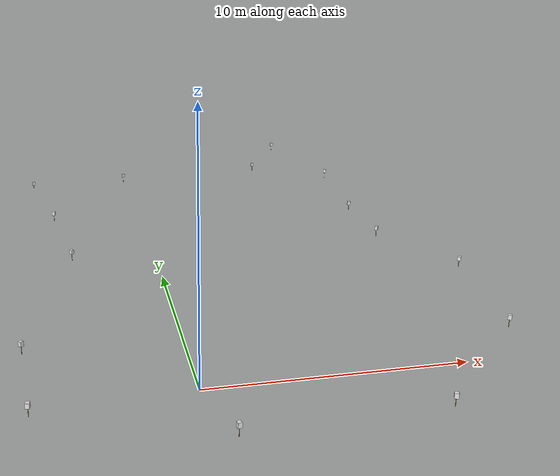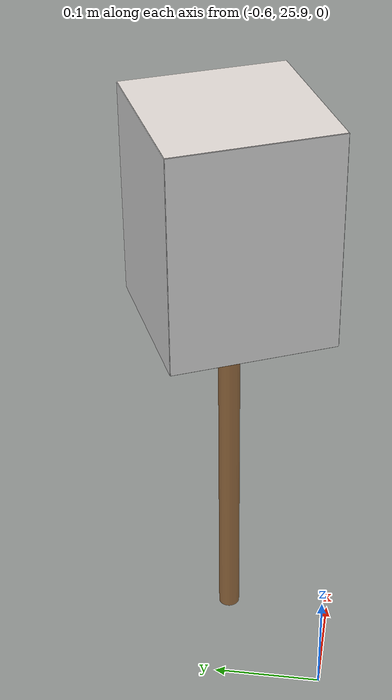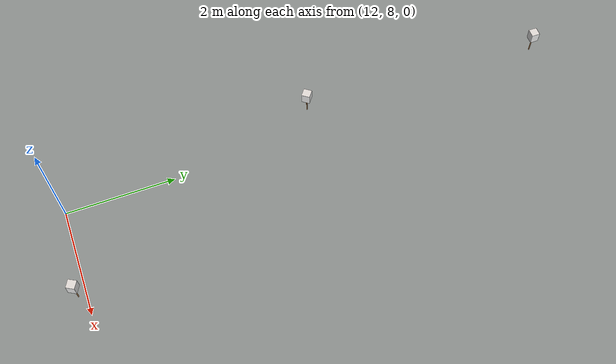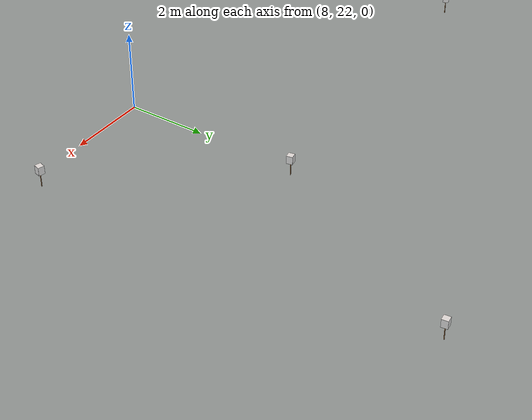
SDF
<sdf version="1.7">
 <world name="mars_yard_2">
  <physics name="10ms" type="ignored">
   <max_step_size>0.01</max_step_size>
   <real_time_factor>1.0</real_time_factor>
  </physics>
  <plugin filename="gz-sim-contact-system" name="gz::sim::systems::Contact"/>
  <plugin filename="gz-sim-imu-system" name="gz::sim::systems::Imu"/>
  <plugin filename="gz-sim-physics-system" name="gz::sim::systems::Physics"/>
  <plugin filename="gz-sim-scene-broadcaster-system" name="gz::sim::systems::SceneBroadcaster"/>
  <plugin filename="gz-sim-sensors-system" name="gz::sim::systems::Sensors"/>
  <plugin filename="gz-sim-user-commands-system" name="gz::sim::systems::UserCommands"/>
  <spherical_coordinates>
   <surface_model>EARTH_WGS84</surface_model>
   <world_frame_orientation>ENU</world_frame_orientation>
   <latitude_deg>50.088384</latitude_deg>
   <longitude_deg>19.939128</longitude_deg>
   <elevation>0</elevation>
   <heading_deg>0</heading_deg>
  </spherical_coordinates>
  <scene><ambient>0.3 0.3 0.3 1</ambient><background>0.6 0.7 0.9 1</background><shadows>true</shadows></scene>
  <light type="directional" name="sun">
   <pose>0 0 10 0 0 0</pose>
   <diffuse>1 1 0.9 1</diffuse>
   <specular>0.2 0.2 0.2 1</specular>
   <attenuation>
    <range>1000</range>
    <constant>0.9</constant>
    <linear>0.01</linear>
    <quadratic>0.001</quadratic>
   </attenuation>
   <direction>-0.5 0.5 -1</direction>
  </light>
  <include><uri>model://aruco_pole_textures/aruco_pole_31</uri><pose>0.75 -2.82 -0.07 0 0 1.852</pose></include>
  <include><uri>model://aruco_pole_textures/aruco_pole_30</uri><pose>8.25 -2.52 -0.10 0 0 4.317</pose></include>
  <include><uri>model://aruco_pole_textures/aruco_pole_29</uri><pose>12.8 1.94 0.20 0 0 0.994</pose></include>
  <include><uri>model://aruco_pole_textures/aruco_pole_28</uri><pose>13.72 7.90 0.26 0 0 5.768</pose></include>
  <include><uri>model://aruco_pole_textures/aruco_pole_27</uri><pose>11.56 12.7 0.23 0 0 2.501</pose></include>
  <include><uri>model://aruco_pole_textures/aruco_pole_26</uri><pose>11.71 17.21 0.16 0 0 3.141</pose></include>
  <include><uri>model://aruco_pole_textures/aruco_pole_25</uri><pose>12.13 22.85 0.50 0 0 6.012</pose></include>
  <include><uri>model://aruco_pole_textures/aruco_pole_24</uri><pose>11.07 32.05 0.09 0 0 0.123</pose></include>
  <include><uri>model://aruco_pole_textures/aruco_pole_23</uri><pose>8.30 26.74 0.09 0 0 4.889</pose></include>
  <include><uri>model://aruco_pole_textures/aruco_pole_22</uri><pose>-0.5 26.0 0.0 0 0 2.007</pose></include>
  <include><uri>model://aruco_pole_textures/aruco_pole_21</uri><pose>-6.2 26.0 -0.22 0 0 5.115</pose></include>
  <include><uri>model://aruco_pole_textures/aruco_pole_20</uri><pose>-4.91 18.41 0.20 0 0 1.166</pose></include>
  <include><uri>model://aruco_pole_textures/aruco_pole_19</uri><pose>-4.07 12.0 0.35 0 0 3.927</pose></include>
  <include><uri>model://aruco_pole_textures/aruco_pole_18</uri><pose>-6.13 3.60 0.09 0 0 0.750</pose></include>
  <include><uri>model://aruco_pole_textures/aruco_pole_17</uri><pose>-5.77 -0.55 0.0 0 0 4.500</pose></include>
 </world>
</sdf>

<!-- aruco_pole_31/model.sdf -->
<sdf version="1.7">
  <!-- Auto-generated SDF for ArUco Pole with Tag 31 -->
  <!-- Box visual faces are 0.1 wide/deep, 0.2 high. Box is closed top/bottom. -->
  <model name="aruco_pole_31"> <!-- Descriptive model name -->
    <static>true</static>
    <link name="aruco_pole_link">

      <!-- === Pole === -->
      <collision name="pole_collision">
        <pose>0 0 0.17250 0 0 0</pose>
        <geometry><cylinder><radius>0.01000</radius><length>0.34500</length></cylinder></geometry>
      </collision>
      <visual name="pole_visual">
        <pose>0 0 0.17250 0 0 0</pose>
        <geometry><cylinder><radius>0.01000</radius><length>0.34500</length></cylinder></geometry>
        <material><script><uri>file://media/materials/scripts/gazebo.material</uri><name>Gazebo/Wood</name></script></material>
      </visual>

      <!-- === Main Marker Box COLLISION === -->
      <!-- Defines the physical boundary -->
      <collision name="box_collision">
        <pose>0 0 0.44500 0 0 0</pose>
        <geometry><box><size>0.15000 0.15000 0.20000</size></box></geometry>
      </collision>

      <!-- === Textured Side Panels (Visuals only) === -->
      <!-- Sized and positioned to match the collision box faces -->

      <!-- Front Face Panel (+X) -->
      <visual name="box_face_front_panel">
        <pose>0.07500 0 0.44500 0 0 0</pose>
        <!-- Size: Thickness(X), Width(Y=Depth), Height(Z) -->
        <geometry><box><size>0.00100 0.15000 0.20000</size></box></geometry>
        <material>
          <ambient>1 1 1 1</ambient><diffuse>1 1 1 1</diffuse><specular>0 0 0 1</specular>
          <pbr><metal>
            <albedo_map>model://aruco_pole_textures/materials/textures/aruco_tag_31.png</albedo_map>
            <metalness>0.0</metalness><roughness>1.0</roughness>
          </metal></pbr>
        </material>
      </visual>

      <!-- Back Face Panel (-X) -->
      <visual name="box_face_back_panel">
        <pose>-0.07500 0 0.44500 0 0 0</pose>
         <!-- Size: Thickness(X), Width(Y=Depth), Height(Z) -->
        <geometry><box><size>0.00100 0.15000 0.20000</size></box></geometry>
         <material>
           <ambient>1 1 1 1</ambient><diffuse>1 1 1 1</diffuse><specular>0 0 0 1</specular>
           <pbr><metal>
             <albedo_map>model://aruco_pole_textures/materials/textures/aruco_tag_31.png</albedo_map>
             <metalness>0.0</metalness><roughness>1.0</roughness>
           </metal></pbr>
         </material>
      </visual>

      <!-- Right Face Panel (+Y) -->
      <visual name="box_face_right_panel">
        <pose>0 0.07500 0.44500 0 0 0</pose>
         <!-- Size: Width(X), Thickness(Y), Height(Z) -->
        <geometry><box><size>0.15000 0.00100 0.20000</size></box></geometry>
         <material>
           <ambient>1 1 1 1</ambient><diffuse>1 1 1 1</diffuse><specular>0 0 0 1</specular>
           <pbr><metal>
             <albedo_map>model://aruco_pole_textures/materials/textures/aruco_tag_31.png</albedo_map>
             <metalness>0.0</metalness><roughness>1.0</roughness>
           </metal></pbr>
         </material>
      </visual>

      <!-- Left Face Panel (-Y) -->
      <visual name="box_face_left_panel">
        <pose>0 -0.07500 0.44500 0 0 0</pose>
        <!-- Size: Width(X), Thickness(Y), Height(Z) -->
        <geometry><box><size>0.15000 0.00100 0.20000</size></box></geometry>
         <material>
           <ambient>1 1 1 1</ambient><diffuse>1 1 1 1</diffuse><specular>0 0 0 1</specular>
           <pbr><metal>
             <albedo_map>model://aruco_pole_textures/materials/textures/aruco_tag_31.png</albedo_map>
             <metalness>0.0</metalness><roughness>1.0</roughness>
           </metal></pbr>
         </material>
      </visual>

      <!-- === Top and Bottom Caps (Visuals only, No Texture) === -->

      <!-- Top Face Panel (+Z) -->
      <visual name="box_face_top_panel">
        <pose>0 0 0.54500 0 0 0</pose>
        <!-- Size: Width(X), Length(Y=Depth), Thickness(Z) -->
        <geometry><box><size>0.15000 0.15000 0.00100</size></box></geometry>
        <material>
          <ambient>0.590 0.571 0.560 1.0</ambient>
          <diffuse>0.843 0.816 0.800 1</diffuse>
          <specular>0.1 0.1 0.1 1</specular>
        </material>
      </visual>

      <!-- Bottom Face Panel (-Z) -->
      <visual name="box_face_bottom_panel">
        <pose>0 0 0.34500 0 0 0</pose>
        <!-- Size: Width(X), Length(Y=Depth), Thickness(Z) -->
        <geometry><box><size>0.15000 0.15000 0.00100</size></box></geometry>
         <material>
           <ambient>0.590 0.571 0.560 1.0</ambient>
           <diffuse>0.843 0.816 0.800 1</diffuse>
           <specular>0.1 0.1 0.1 1</specular>
         </material>
      </visual>

    </link>
  </model>
</sdf>

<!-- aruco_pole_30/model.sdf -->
<sdf version="1.7">
  <!-- Auto-generated SDF for ArUco Pole with Tag 30 -->
  <!-- Box visual faces are 0.1 wide/deep, 0.2 high. Box is closed top/bottom. -->
  <model name="aruco_pole_30"> <!-- Descriptive model name -->
    <static>true</static>
    <link name="aruco_pole_link">

      <!-- === Pole === -->
      <collision name="pole_collision">
        <pose>0 0 0.17250 0 0 0</pose>
        <geometry><cylinder><radius>0.01000</radius><length>0.34500</length></cylinder></geometry>
      </collision>
      <visual name="pole_visual">
        <pose>0 0 0.17250 0 0 0</pose>
        <geometry><cylinder><radius>0.01000</radius><length>0.34500</length></cylinder></geometry>
        <material><script><uri>file://media/materials/scripts/gazebo.material</uri><name>Gazebo/Wood</name></script></material>
      </visual>

      <!-- === Main Marker Box COLLISION === -->
      <!-- Defines the physical boundary -->
      <collision name="box_collision">
        <pose>0 0 0.44500 0 0 0</pose>
        <geometry><box><size>0.15000 0.15000 0.20000</size></box></geometry>
      </collision>

      <!-- === Textured Side Panels (Visuals only) === -->
      <!-- Sized and positioned to match the collision box faces -->

      <!-- Front Face Panel (+X) -->
      <visual name="box_face_front_panel">
        <pose>0.07500 0 0.44500 0 0 0</pose>
        <!-- Size: Thickness(X), Width(Y=Depth), Height(Z) -->
        <geometry><box><size>0.00100 0.15000 0.20000</size></box></geometry>
        <material>
          <ambient>1 1 1 1</ambient><diffuse>1 1 1 1</diffuse><specular>0 0 0 1</specular>
          <pbr><metal>
            <albedo_map>model://aruco_pole_textures/materials/textures/aruco_tag_30.png</albedo_map>
            <metalness>0.0</metalness><roughness>1.0</roughness>
          </metal></pbr>
        </material>
      </visual>

      <!-- Back Face Panel (-X) -->
      <visual name="box_face_back_panel">
        <pose>-0.07500 0 0.44500 0 0 0</pose>
         <!-- Size: Thickness(X), Width(Y=Depth), Height(Z) -->
        <geometry><box><size>0.00100 0.15000 0.20000</size></box></geometry>
         <material>
           <ambient>1 1 1 1</ambient><diffuse>1 1 1 1</diffuse><specular>0 0 0 1</specular>
           <pbr><metal>
             <albedo_map>model://aruco_pole_textures/materials/textures/aruco_tag_30.png</albedo_map>
             <metalness>0.0</metalness><roughness>1.0</roughness>
           </metal></pbr>
         </material>
      </visual>

      <!-- Right Face Panel (+Y) -->
      <visual name="box_face_right_panel">
        <pose>0 0.07500 0.44500 0 0 0</pose>
         <!-- Size: Width(X), Thickness(Y), Height(Z) -->
        <geometry><box><size>0.15000 0.00100 0.20000</size></box></geometry>
         <material>
           <ambient>1 1 1 1</ambient><diffuse>1 1 1 1</diffuse><specular>0 0 0 1</specular>
           <pbr><metal>
             <albedo_map>model://aruco_pole_textures/materials/textures/aruco_tag_30.png</albedo_map>
             <metalness>0.0</metalness><roughness>1.0</roughness>
           </metal></pbr>
         </material>
      </visual>

      <!-- Left Face Panel (-Y) -->
      <visual name="box_face_left_panel">
        <pose>0 -0.07500 0.44500 0 0 0</pose>
        <!-- Size: Width(X), Thickness(Y), Height(Z) -->
        <geometry><box><size>0.15000 0.00100 0.20000</size></box></geometry>
         <material>
           <ambient>1 1 1 1</ambient><diffuse>1 1 1 1</diffuse><specular>0 0 0 1</specular>
           <pbr><metal>
             <albedo_map>model://aruco_pole_textures/materials/textures/aruco_tag_30.png</albedo_map>
             <metalness>0.0</metalness><roughness>1.0</roughness>
           </metal></pbr>
         </material>
      </visual>

      <!-- === Top and Bottom Caps (Visuals only, No Texture) === -->

      <!-- Top Face Panel (+Z) -->
      <visual name="box_face_top_panel">
        <pose>0 0 0.54500 0 0 0</pose>
        <!-- Size: Width(X), Length(Y=Depth), Thickness(Z) -->
        <geometry><box><size>0.15000 0.15000 0.00100</size></box></geometry>
        <material>
          <ambient>0.590 0.571 0.560 1.0</ambient>
          <diffuse>0.843 0.816 0.800 1</diffuse>
          <specular>0.1 0.1 0.1 1</specular>
        </material>
      </visual>

      <!-- Bottom Face Panel (-Z) -->
      <visual name="box_face_bottom_panel">
        <pose>0 0 0.34500 0 0 0</pose>
        <!-- Size: Width(X), Length(Y=Depth), Thickness(Z) -->
        <geometry><box><size>0.15000 0.15000 0.00100</size></box></geometry>
         <material>
           <ambient>0.590 0.571 0.560 1.0</ambient>
           <diffuse>0.843 0.816 0.800 1</diffuse>
           <specular>0.1 0.1 0.1 1</specular>
         </material>
      </visual>

    </link>
  </model>
</sdf>

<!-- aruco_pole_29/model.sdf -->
<sdf version="1.7">
  <!-- Auto-generated SDF for ArUco Pole with Tag 29 -->
  <!-- Box visual faces are 0.1 wide/deep, 0.2 high. Box is closed top/bottom. -->
  <model name="aruco_pole_29"> <!-- Descriptive model name -->
    <static>true</static>
    <link name="aruco_pole_link">

      <!-- === Pole === -->
      <collision name="pole_collision">
        <pose>0 0 0.17250 0 0 0</pose>
        <geometry><cylinder><radius>0.01000</radius><length>0.34500</length></cylinder></geometry>
      </collision>
      <visual name="pole_visual">
        <pose>0 0 0.17250 0 0 0</pose>
        <geometry><cylinder><radius>0.01000</radius><length>0.34500</length></cylinder></geometry>
        <material><script><uri>file://media/materials/scripts/gazebo.material</uri><name>Gazebo/Wood</name></script></material>
      </visual>

      <!-- === Main Marker Box COLLISION === -->
      <!-- Defines the physical boundary -->
      <collision name="box_collision">
        <pose>0 0 0.44500 0 0 0</pose>
        <geometry><box><size>0.15000 0.15000 0.20000</size></box></geometry>
      </collision>

      <!-- === Textured Side Panels (Visuals only) === -->
      <!-- Sized and positioned to match the collision box faces -->

      <!-- Front Face Panel (+X) -->
      <visual name="box_face_front_panel">
        <pose>0.07500 0 0.44500 0 0 0</pose>
        <!-- Size: Thickness(X), Width(Y=Depth), Height(Z) -->
        <geometry><box><size>0.00100 0.15000 0.20000</size></box></geometry>
        <material>
          <ambient>1 1 1 1</ambient><diffuse>1 1 1 1</diffuse><specular>0 0 0 1</specular>
          <pbr><metal>
            <albedo_map>model://aruco_pole_textures/materials/textures/aruco_tag_29.png</albedo_map>
            <metalness>0.0</metalness><roughness>1.0</roughness>
          </metal></pbr>
        </material>
      </visual>

      <!-- Back Face Panel (-X) -->
      <visual name="box_face_back_panel">
        <pose>-0.07500 0 0.44500 0 0 0</pose>
         <!-- Size: Thickness(X), Width(Y=Depth), Height(Z) -->
        <geometry><box><size>0.00100 0.15000 0.20000</size></box></geometry>
         <material>
           <ambient>1 1 1 1</ambient><diffuse>1 1 1 1</diffuse><specular>0 0 0 1</specular>
           <pbr><metal>
             <albedo_map>model://aruco_pole_textures/materials/textures/aruco_tag_29.png</albedo_map>
             <metalness>0.0</metalness><roughness>1.0</roughness>
           </metal></pbr>
         </material>
      </visual>

      <!-- Right Face Panel (+Y) -->
      <visual name="box_face_right_panel">
        <pose>0 0.07500 0.44500 0 0 0</pose>
         <!-- Size: Width(X), Thickness(Y), Height(Z) -->
        <geometry><box><size>0.15000 0.00100 0.20000</size></box></geometry>
         <material>
           <ambient>1 1 1 1</ambient><diffuse>1 1 1 1</diffuse><specular>0 0 0 1</specular>
           <pbr><metal>
             <albedo_map>model://aruco_pole_textures/materials/textures/aruco_tag_29.png</albedo_map>
             <metalness>0.0</metalness><roughness>1.0</roughness>
           </metal></pbr>
         </material>
      </visual>

      <!-- Left Face Panel (-Y) -->
      <visual name="box_face_left_panel">
        <pose>0 -0.07500 0.44500 0 0 0</pose>
        <!-- Size: Width(X), Thickness(Y), Height(Z) -->
        <geometry><box><size>0.15000 0.00100 0.20000</size></box></geometry>
         <material>
           <ambient>1 1 1 1</ambient><diffuse>1 1 1 1</diffuse><specular>0 0 0 1</specular>
           <pbr><metal>
             <albedo_map>model://aruco_pole_textures/materials/textures/aruco_tag_29.png</albedo_map>
             <metalness>0.0</metalness><roughness>1.0</roughness>
           </metal></pbr>
         </material>
      </visual>

      <!-- === Top and Bottom Caps (Visuals only, No Texture) === -->

      <!-- Top Face Panel (+Z) -->
      <visual name="box_face_top_panel">
        <pose>0 0 0.54500 0 0 0</pose>
        <!-- Size: Width(X), Length(Y=Depth), Thickness(Z) -->
        <geometry><box><size>0.15000 0.15000 0.00100</size></box></geometry>
        <material>
          <ambient>0.590 0.571 0.560 1.0</ambient>
          <diffuse>0.843 0.816 0.800 1</diffuse>
          <specular>0.1 0.1 0.1 1</specular>
        </material>
      </visual>

      <!-- Bottom Face Panel (-Z) -->
      <visual name="box_face_bottom_panel">
        <pose>0 0 0.34500 0 0 0</pose>
        <!-- Size: Width(X), Length(Y=Depth), Thickness(Z) -->
        <geometry><box><size>0.15000 0.15000 0.00100</size></box></geometry>
         <material>
           <ambient>0.590 0.571 0.560 1.0</ambient>
           <diffuse>0.843 0.816 0.800 1</diffuse>
           <specular>0.1 0.1 0.1 1</specular>
         </material>
      </visual>

    </link>
  </model>
</sdf>

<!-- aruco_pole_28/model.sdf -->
<sdf version="1.7">
  <!-- Auto-generated SDF for ArUco Pole with Tag 28 -->
  <!-- Box visual faces are 0.1 wide/deep, 0.2 high. Box is closed top/bottom. -->
  <model name="aruco_pole_28"> <!-- Descriptive model name -->
    <static>true</static>
    <link name="aruco_pole_link">

      <!-- === Pole === -->
      <collision name="pole_collision">
        <pose>0 0 0.17250 0 0 0</pose>
        <geometry><cylinder><radius>0.01000</radius><length>0.34500</length></cylinder></geometry>
      </collision>
      <visual name="pole_visual">
        <pose>0 0 0.17250 0 0 0</pose>
        <geometry><cylinder><radius>0.01000</radius><length>0.34500</length></cylinder></geometry>
        <material><script><uri>file://media/materials/scripts/gazebo.material</uri><name>Gazebo/Wood</name></script></material>
      </visual>

      <!-- === Main Marker Box COLLISION === -->
      <!-- Defines the physical boundary -->
      <collision name="box_collision">
        <pose>0 0 0.44500 0 0 0</pose>
        <geometry><box><size>0.15000 0.15000 0.20000</size></box></geometry>
      </collision>

      <!-- === Textured Side Panels (Visuals only) === -->
      <!-- Sized and positioned to match the collision box faces -->

      <!-- Front Face Panel (+X) -->
      <visual name="box_face_front_panel">
        <pose>0.07500 0 0.44500 0 0 0</pose>
        <!-- Size: Thickness(X), Width(Y=Depth), Height(Z) -->
        <geometry><box><size>0.00100 0.15000 0.20000</size></box></geometry>
        <material>
          <ambient>1 1 1 1</ambient><diffuse>1 1 1 1</diffuse><specular>0 0 0 1</specular>
          <pbr><metal>
            <albedo_map>model://aruco_pole_textures/materials/textures/aruco_tag_28.png</albedo_map>
            <metalness>0.0</metalness><roughness>1.0</roughness>
          </metal></pbr>
        </material>
      </visual>

      <!-- Back Face Panel (-X) -->
      <visual name="box_face_back_panel">
        <pose>-0.07500 0 0.44500 0 0 0</pose>
         <!-- Size: Thickness(X), Width(Y=Depth), Height(Z) -->
        <geometry><box><size>0.00100 0.15000 0.20000</size></box></geometry>
         <material>
           <ambient>1 1 1 1</ambient><diffuse>1 1 1 1</diffuse><specular>0 0 0 1</specular>
           <pbr><metal>
             <albedo_map>model://aruco_pole_textures/materials/textures/aruco_tag_28.png</albedo_map>
             <metalness>0.0</metalness><roughness>1.0</roughness>
           </metal></pbr>
         </material>
      </visual>

      <!-- Right Face Panel (+Y) -->
      <visual name="box_face_right_panel">
        <pose>0 0.07500 0.44500 0 0 0</pose>
         <!-- Size: Width(X), Thickness(Y), Height(Z) -->
        <geometry><box><size>0.15000 0.00100 0.20000</size></box></geometry>
         <material>
           <ambient>1 1 1 1</ambient><diffuse>1 1 1 1</diffuse><specular>0 0 0 1</specular>
           <pbr><metal>
             <albedo_map>model://aruco_pole_textures/materials/textures/aruco_tag_28.png</albedo_map>
             <metalness>0.0</metalness><roughness>1.0</roughness>
           </metal></pbr>
         </material>
      </visual>

      <!-- Left Face Panel (-Y) -->
      <visual name="box_face_left_panel">
        <pose>0 -0.07500 0.44500 0 0 0</pose>
        <!-- Size: Width(X), Thickness(Y), Height(Z) -->
        <geometry><box><size>0.15000 0.00100 0.20000</size></box></geometry>
         <material>
           <ambient>1 1 1 1</ambient><diffuse>1 1 1 1</diffuse><specular>0 0 0 1</specular>
           <pbr><metal>
             <albedo_map>model://aruco_pole_textures/materials/textures/aruco_tag_28.png</albedo_map>
             <metalness>0.0</metalness><roughness>1.0</roughness>
           </metal></pbr>
         </material>
      </visual>

      <!-- === Top and Bottom Caps (Visuals only, No Texture) === -->

      <!-- Top Face Panel (+Z) -->
      <visual name="box_face_top_panel">
        <pose>0 0 0.54500 0 0 0</pose>
        <!-- Size: Width(X), Length(Y=Depth), Thickness(Z) -->
        <geometry><box><size>0.15000 0.15000 0.00100</size></box></geometry>
        <material>
          <ambient>0.590 0.571 0.560 1.0</ambient>
          <diffuse>0.843 0.816 0.800 1</diffuse>
          <specular>0.1 0.1 0.1 1</specular>
        </material>
      </visual>

      <!-- Bottom Face Panel (-Z) -->
      <visual name="box_face_bottom_panel">
        <pose>0 0 0.34500 0 0 0</pose>
        <!-- Size: Width(X), Length(Y=Depth), Thickness(Z) -->
        <geometry><box><size>0.15000 0.15000 0.00100</size></box></geometry>
         <material>
           <ambient>0.590 0.571 0.560 1.0</ambient>
           <diffuse>0.843 0.816 0.800 1</diffuse>
           <specular>0.1 0.1 0.1 1</specular>
         </material>
      </visual>

    </link>
  </model>
</sdf>

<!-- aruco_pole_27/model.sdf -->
<sdf version="1.7">
  <!-- Auto-generated SDF for ArUco Pole with Tag 27 -->
  <!-- Box visual faces are 0.1 wide/deep, 0.2 high. Box is closed top/bottom. -->
  <model name="aruco_pole_27"> <!-- Descriptive model name -->
    <static>true</static>
    <link name="aruco_pole_link">

      <!-- === Pole === -->
      <collision name="pole_collision">
        <pose>0 0 0.17250 0 0 0</pose>
        <geometry><cylinder><radius>0.01000</radius><length>0.34500</length></cylinder></geometry>
      </collision>
      <visual name="pole_visual">
        <pose>0 0 0.17250 0 0 0</pose>
        <geometry><cylinder><radius>0.01000</radius><length>0.34500</length></cylinder></geometry>
        <material><script><uri>file://media/materials/scripts/gazebo.material</uri><name>Gazebo/Wood</name></script></material>
      </visual>

      <!-- === Main Marker Box COLLISION === -->
      <!-- Defines the physical boundary -->
      <collision name="box_collision">
        <pose>0 0 0.44500 0 0 0</pose>
        <geometry><box><size>0.15000 0.15000 0.20000</size></box></geometry>
      </collision>

      <!-- === Textured Side Panels (Visuals only) === -->
      <!-- Sized and positioned to match the collision box faces -->

      <!-- Front Face Panel (+X) -->
      <visual name="box_face_front_panel">
        <pose>0.07500 0 0.44500 0 0 0</pose>
        <!-- Size: Thickness(X), Width(Y=Depth), Height(Z) -->
        <geometry><box><size>0.00100 0.15000 0.20000</size></box></geometry>
        <material>
          <ambient>1 1 1 1</ambient><diffuse>1 1 1 1</diffuse><specular>0 0 0 1</specular>
          <pbr><metal>
            <albedo_map>model://aruco_pole_textures/materials/textures/aruco_tag_27.png</albedo_map>
            <metalness>0.0</metalness><roughness>1.0</roughness>
          </metal></pbr>
        </material>
      </visual>

      <!-- Back Face Panel (-X) -->
      <visual name="box_face_back_panel">
        <pose>-0.07500 0 0.44500 0 0 0</pose>
         <!-- Size: Thickness(X), Width(Y=Depth), Height(Z) -->
        <geometry><box><size>0.00100 0.15000 0.20000</size></box></geometry>
         <material>
           <ambient>1 1 1 1</ambient><diffuse>1 1 1 1</diffuse><specular>0 0 0 1</specular>
           <pbr><metal>
             <albedo_map>model://aruco_pole_textures/materials/textures/aruco_tag_27.png</albedo_map>
             <metalness>0.0</metalness><roughness>1.0</roughness>
           </metal></pbr>
         </material>
      </visual>

      <!-- Right Face Panel (+Y) -->
      <visual name="box_face_right_panel">
        <pose>0 0.07500 0.44500 0 0 0</pose>
         <!-- Size: Width(X), Thickness(Y), Height(Z) -->
        <geometry><box><size>0.15000 0.00100 0.20000</size></box></geometry>
         <material>
           <ambient>1 1 1 1</ambient><diffuse>1 1 1 1</diffuse><specular>0 0 0 1</specular>
           <pbr><metal>
             <albedo_map>model://aruco_pole_textures/materials/textures/aruco_tag_27.png</albedo_map>
             <metalness>0.0</metalness><roughness>1.0</roughness>
           </metal></pbr>
         </material>
      </visual>

      <!-- Left Face Panel (-Y) -->
      <visual name="box_face_left_panel">
        <pose>0 -0.07500 0.44500 0 0 0</pose>
        <!-- Size: Width(X), Thickness(Y), Height(Z) -->
        <geometry><box><size>0.15000 0.00100 0.20000</size></box></geometry>
         <material>
           <ambient>1 1 1 1</ambient><diffuse>1 1 1 1</diffuse><specular>0 0 0 1</specular>
           <pbr><metal>
             <albedo_map>model://aruco_pole_textures/materials/textures/aruco_tag_27.png</albedo_map>
             <metalness>0.0</metalness><roughness>1.0</roughness>
           </metal></pbr>
         </material>
      </visual>

      <!-- === Top and Bottom Caps (Visuals only, No Texture) === -->

      <!-- Top Face Panel (+Z) -->
      <visual name="box_face_top_panel">
        <pose>0 0 0.54500 0 0 0</pose>
        <!-- Size: Width(X), Length(Y=Depth), Thickness(Z) -->
        <geometry><box><size>0.15000 0.15000 0.00100</size></box></geometry>
        <material>
          <ambient>0.590 0.571 0.560 1.0</ambient>
          <diffuse>0.843 0.816 0.800 1</diffuse>
          <specular>0.1 0.1 0.1 1</specular>
        </material>
      </visual>

      <!-- Bottom Face Panel (-Z) -->
      <visual name="box_face_bottom_panel">
        <pose>0 0 0.34500 0 0 0</pose>
        <!-- Size: Width(X), Length(Y=Depth), Thickness(Z) -->
        <geometry><box><size>0.15000 0.15000 0.00100</size></box></geometry>
         <material>
           <ambient>0.590 0.571 0.560 1.0</ambient>
           <diffuse>0.843 0.816 0.800 1</diffuse>
           <specular>0.1 0.1 0.1 1</specular>
         </material>
      </visual>

    </link>
  </model>
</sdf>

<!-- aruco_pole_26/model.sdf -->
<sdf version="1.7">
  <!-- Auto-generated SDF for ArUco Pole with Tag 26 -->
  <!-- Box visual faces are 0.1 wide/deep, 0.2 high. Box is closed top/bottom. -->
  <model name="aruco_pole_26"> <!-- Descriptive model name -->
    <static>true</static>
    <link name="aruco_pole_link">

      <!-- === Pole === -->
      <collision name="pole_collision">
        <pose>0 0 0.17250 0 0 0</pose>
        <geometry><cylinder><radius>0.01000</radius><length>0.34500</length></cylinder></geometry>
      </collision>
      <visual name="pole_visual">
        <pose>0 0 0.17250 0 0 0</pose>
        <geometry><cylinder><radius>0.01000</radius><length>0.34500</length></cylinder></geometry>
        <material><script><uri>file://media/materials/scripts/gazebo.material</uri><name>Gazebo/Wood</name></script></material>
      </visual>

      <!-- === Main Marker Box COLLISION === -->
      <!-- Defines the physical boundary -->
      <collision name="box_collision">
        <pose>0 0 0.44500 0 0 0</pose>
        <geometry><box><size>0.15000 0.15000 0.20000</size></box></geometry>
      </collision>

      <!-- === Textured Side Panels (Visuals only) === -->
      <!-- Sized and positioned to match the collision box faces -->

      <!-- Front Face Panel (+X) -->
      <visual name="box_face_front_panel">
        <pose>0.07500 0 0.44500 0 0 0</pose>
        <!-- Size: Thickness(X), Width(Y=Depth), Height(Z) -->
        <geometry><box><size>0.00100 0.15000 0.20000</size></box></geometry>
        <material>
          <ambient>1 1 1 1</ambient><diffuse>1 1 1 1</diffuse><specular>0 0 0 1</specular>
          <pbr><metal>
            <albedo_map>model://aruco_pole_textures/materials/textures/aruco_tag_26.png</albedo_map>
            <metalness>0.0</metalness><roughness>1.0</roughness>
          </metal></pbr>
        </material>
      </visual>

      <!-- Back Face Panel (-X) -->
      <visual name="box_face_back_panel">
        <pose>-0.07500 0 0.44500 0 0 0</pose>
         <!-- Size: Thickness(X), Width(Y=Depth), Height(Z) -->
        <geometry><box><size>0.00100 0.15000 0.20000</size></box></geometry>
         <material>
           <ambient>1 1 1 1</ambient><diffuse>1 1 1 1</diffuse><specular>0 0 0 1</specular>
           <pbr><metal>
             <albedo_map>model://aruco_pole_textures/materials/textures/aruco_tag_26.png</albedo_map>
             <metalness>0.0</metalness><roughness>1.0</roughness>
           </metal></pbr>
         </material>
      </visual>

      <!-- Right Face Panel (+Y) -->
      <visual name="box_face_right_panel">
        <pose>0 0.07500 0.44500 0 0 0</pose>
         <!-- Size: Width(X), Thickness(Y), Height(Z) -->
        <geometry><box><size>0.15000 0.00100 0.20000</size></box></geometry>
         <material>
           <ambient>1 1 1 1</ambient><diffuse>1 1 1 1</diffuse><specular>0 0 0 1</specular>
           <pbr><metal>
             <albedo_map>model://aruco_pole_textures/materials/textures/aruco_tag_26.png</albedo_map>
             <metalness>0.0</metalness><roughness>1.0</roughness>
           </metal></pbr>
         </material>
      </visual>

      <!-- Left Face Panel (-Y) -->
      <visual name="box_face_left_panel">
        <pose>0 -0.07500 0.44500 0 0 0</pose>
        <!-- Size: Width(X), Thickness(Y), Height(Z) -->
        <geometry><box><size>0.15000 0.00100 0.20000</size></box></geometry>
         <material>
           <ambient>1 1 1 1</ambient><diffuse>1 1 1 1</diffuse><specular>0 0 0 1</specular>
           <pbr><metal>
             <albedo_map>model://aruco_pole_textures/materials/textures/aruco_tag_26.png</albedo_map>
             <metalness>0.0</metalness><roughness>1.0</roughness>
           </metal></pbr>
         </material>
      </visual>

      <!-- === Top and Bottom Caps (Visuals only, No Texture) === -->

      <!-- Top Face Panel (+Z) -->
      <visual name="box_face_top_panel">
        <pose>0 0 0.54500 0 0 0</pose>
        <!-- Size: Width(X), Length(Y=Depth), Thickness(Z) -->
        <geometry><box><size>0.15000 0.15000 0.00100</size></box></geometry>
        <material>
          <ambient>0.590 0.571 0.560 1.0</ambient>
          <diffuse>0.843 0.816 0.800 1</diffuse>
          <specular>0.1 0.1 0.1 1</specular>
        </material>
      </visual>

      <!-- Bottom Face Panel (-Z) -->
      <visual name="box_face_bottom_panel">
        <pose>0 0 0.34500 0 0 0</pose>
        <!-- Size: Width(X), Length(Y=Depth), Thickness(Z) -->
        <geometry><box><size>0.15000 0.15000 0.00100</size></box></geometry>
         <material>
           <ambient>0.590 0.571 0.560 1.0</ambient>
           <diffuse>0.843 0.816 0.800 1</diffuse>
           <specular>0.1 0.1 0.1 1</specular>
         </material>
      </visual>

    </link>
  </model>
</sdf>

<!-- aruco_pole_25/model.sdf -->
<sdf version="1.7">
  <!-- Auto-generated SDF for ArUco Pole with Tag 25 -->
  <!-- Box visual faces are 0.1 wide/deep, 0.2 high. Box is closed top/bottom. -->
  <model name="aruco_pole_25"> <!-- Descriptive model name -->
    <static>true</static>
    <link name="aruco_pole_link">

      <!-- === Pole === -->
      <collision name="pole_collision">
        <pose>0 0 0.17250 0 0 0</pose>
        <geometry><cylinder><radius>0.01000</radius><length>0.34500</length></cylinder></geometry>
      </collision>
      <visual name="pole_visual">
        <pose>0 0 0.17250 0 0 0</pose>
        <geometry><cylinder><radius>0.01000</radius><length>0.34500</length></cylinder></geometry>
        <material><script><uri>file://media/materials/scripts/gazebo.material</uri><name>Gazebo/Wood</name></script></material>
      </visual>

      <!-- === Main Marker Box COLLISION === -->
      <!-- Defines the physical boundary -->
      <collision name="box_collision">
        <pose>0 0 0.44500 0 0 0</pose>
        <geometry><box><size>0.15000 0.15000 0.20000</size></box></geometry>
      </collision>

      <!-- === Textured Side Panels (Visuals only) === -->
      <!-- Sized and positioned to match the collision box faces -->

      <!-- Front Face Panel (+X) -->
      <visual name="box_face_front_panel">
        <pose>0.07500 0 0.44500 0 0 0</pose>
        <!-- Size: Thickness(X), Width(Y=Depth), Height(Z) -->
        <geometry><box><size>0.00100 0.15000 0.20000</size></box></geometry>
        <material>
          <ambient>1 1 1 1</ambient><diffuse>1 1 1 1</diffuse><specular>0 0 0 1</specular>
          <pbr><metal>
            <albedo_map>model://aruco_pole_textures/materials/textures/aruco_tag_25.png</albedo_map>
            <metalness>0.0</metalness><roughness>1.0</roughness>
          </metal></pbr>
        </material>
      </visual>

      <!-- Back Face Panel (-X) -->
      <visual name="box_face_back_panel">
        <pose>-0.07500 0 0.44500 0 0 0</pose>
         <!-- Size: Thickness(X), Width(Y=Depth), Height(Z) -->
        <geometry><box><size>0.00100 0.15000 0.20000</size></box></geometry>
         <material>
           <ambient>1 1 1 1</ambient><diffuse>1 1 1 1</diffuse><specular>0 0 0 1</specular>
           <pbr><metal>
             <albedo_map>model://aruco_pole_textures/materials/textures/aruco_tag_25.png</albedo_map>
             <metalness>0.0</metalness><roughness>1.0</roughness>
           </metal></pbr>
         </material>
      </visual>

      <!-- Right Face Panel (+Y) -->
      <visual name="box_face_right_panel">
        <pose>0 0.07500 0.44500 0 0 0</pose>
         <!-- Size: Width(X), Thickness(Y), Height(Z) -->
        <geometry><box><size>0.15000 0.00100 0.20000</size></box></geometry>
         <material>
           <ambient>1 1 1 1</ambient><diffuse>1 1 1 1</diffuse><specular>0 0 0 1</specular>
           <pbr><metal>
             <albedo_map>model://aruco_pole_textures/materials/textures/aruco_tag_25.png</albedo_map>
             <metalness>0.0</metalness><roughness>1.0</roughness>
           </metal></pbr>
         </material>
      </visual>

      <!-- Left Face Panel (-Y) -->
      <visual name="box_face_left_panel">
        <pose>0 -0.07500 0.44500 0 0 0</pose>
        <!-- Size: Width(X), Thickness(Y), Height(Z) -->
        <geometry><box><size>0.15000 0.00100 0.20000</size></box></geometry>
         <material>
           <ambient>1 1 1 1</ambient><diffuse>1 1 1 1</diffuse><specular>0 0 0 1</specular>
           <pbr><metal>
             <albedo_map>model://aruco_pole_textures/materials/textures/aruco_tag_25.png</albedo_map>
             <metalness>0.0</metalness><roughness>1.0</roughness>
           </metal></pbr>
         </material>
      </visual>

      <!-- === Top and Bottom Caps (Visuals only, No Texture) === -->

      <!-- Top Face Panel (+Z) -->
      <visual name="box_face_top_panel">
        <pose>0 0 0.54500 0 0 0</pose>
        <!-- Size: Width(X), Length(Y=Depth), Thickness(Z) -->
        <geometry><box><size>0.15000 0.15000 0.00100</size></box></geometry>
        <material>
          <ambient>0.590 0.571 0.560 1.0</ambient>
          <diffuse>0.843 0.816 0.800 1</diffuse>
          <specular>0.1 0.1 0.1 1</specular>
        </material>
      </visual>

      <!-- Bottom Face Panel (-Z) -->
      <visual name="box_face_bottom_panel">
        <pose>0 0 0.34500 0 0 0</pose>
        <!-- Size: Width(X), Length(Y=Depth), Thickness(Z) -->
        <geometry><box><size>0.15000 0.15000 0.00100</size></box></geometry>
         <material>
           <ambient>0.590 0.571 0.560 1.0</ambient>
           <diffuse>0.843 0.816 0.800 1</diffuse>
           <specular>0.1 0.1 0.1 1</specular>
         </material>
      </visual>

    </link>
  </model>
</sdf>

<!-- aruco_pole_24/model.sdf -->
<sdf version="1.7">
  <!-- Auto-generated SDF for ArUco Pole with Tag 24 -->
  <!-- Box visual faces are 0.1 wide/deep, 0.2 high. Box is closed top/bottom. -->
  <model name="aruco_pole_24"> <!-- Descriptive model name -->
    <static>true</static>
    <link name="aruco_pole_link">

      <!-- === Pole === -->
      <collision name="pole_collision">
        <pose>0 0 0.17250 0 0 0</pose>
        <geometry><cylinder><radius>0.01000</radius><length>0.34500</length></cylinder></geometry>
      </collision>
      <visual name="pole_visual">
        <pose>0 0 0.17250 0 0 0</pose>
        <geometry><cylinder><radius>0.01000</radius><length>0.34500</length></cylinder></geometry>
        <material><script><uri>file://media/materials/scripts/gazebo.material</uri><name>Gazebo/Wood</name></script></material>
      </visual>

      <!-- === Main Marker Box COLLISION === -->
      <!-- Defines the physical boundary -->
      <collision name="box_collision">
        <pose>0 0 0.44500 0 0 0</pose>
        <geometry><box><size>0.15000 0.15000 0.20000</size></box></geometry>
      </collision>

      <!-- === Textured Side Panels (Visuals only) === -->
      <!-- Sized and positioned to match the collision box faces -->

      <!-- Front Face Panel (+X) -->
      <visual name="box_face_front_panel">
        <pose>0.07500 0 0.44500 0 0 0</pose>
        <!-- Size: Thickness(X), Width(Y=Depth), Height(Z) -->
        <geometry><box><size>0.00100 0.15000 0.20000</size></box></geometry>
        <material>
          <ambient>1 1 1 1</ambient><diffuse>1 1 1 1</diffuse><specular>0 0 0 1</specular>
          <pbr><metal>
            <albedo_map>model://aruco_pole_textures/materials/textures/aruco_tag_24.png</albedo_map>
            <metalness>0.0</metalness><roughness>1.0</roughness>
          </metal></pbr>
        </material>
      </visual>

      <!-- Back Face Panel (-X) -->
      <visual name="box_face_back_panel">
        <pose>-0.07500 0 0.44500 0 0 0</pose>
         <!-- Size: Thickness(X), Width(Y=Depth), Height(Z) -->
        <geometry><box><size>0.00100 0.15000 0.20000</size></box></geometry>
         <material>
           <ambient>1 1 1 1</ambient><diffuse>1 1 1 1</diffuse><specular>0 0 0 1</specular>
           <pbr><metal>
             <albedo_map>model://aruco_pole_textures/materials/textures/aruco_tag_24.png</albedo_map>
             <metalness>0.0</metalness><roughness>1.0</roughness>
           </metal></pbr>
         </material>
      </visual>

      <!-- Right Face Panel (+Y) -->
      <visual name="box_face_right_panel">
        <pose>0 0.07500 0.44500 0 0 0</pose>
         <!-- Size: Width(X), Thickness(Y), Height(Z) -->
        <geometry><box><size>0.15000 0.00100 0.20000</size></box></geometry>
         <material>
           <ambient>1 1 1 1</ambient><diffuse>1 1 1 1</diffuse><specular>0 0 0 1</specular>
           <pbr><metal>
             <albedo_map>model://aruco_pole_textures/materials/textures/aruco_tag_24.png</albedo_map>
             <metalness>0.0</metalness><roughness>1.0</roughness>
           </metal></pbr>
         </material>
      </visual>

      <!-- Left Face Panel (-Y) -->
      <visual name="box_face_left_panel">
        <pose>0 -0.07500 0.44500 0 0 0</pose>
        <!-- Size: Width(X), Thickness(Y), Height(Z) -->
        <geometry><box><size>0.15000 0.00100 0.20000</size></box></geometry>
         <material>
           <ambient>1 1 1 1</ambient><diffuse>1 1 1 1</diffuse><specular>0 0 0 1</specular>
           <pbr><metal>
             <albedo_map>model://aruco_pole_textures/materials/textures/aruco_tag_24.png</albedo_map>
             <metalness>0.0</metalness><roughness>1.0</roughness>
           </metal></pbr>
         </material>
      </visual>

      <!-- === Top and Bottom Caps (Visuals only, No Texture) === -->

      <!-- Top Face Panel (+Z) -->
      <visual name="box_face_top_panel">
        <pose>0 0 0.54500 0 0 0</pose>
        <!-- Size: Width(X), Length(Y=Depth), Thickness(Z) -->
        <geometry><box><size>0.15000 0.15000 0.00100</size></box></geometry>
        <material>
          <ambient>0.590 0.571 0.560 1.0</ambient>
          <diffuse>0.843 0.816 0.800 1</diffuse>
          <specular>0.1 0.1 0.1 1</specular>
        </material>
      </visual>

      <!-- Bottom Face Panel (-Z) -->
      <visual name="box_face_bottom_panel">
        <pose>0 0 0.34500 0 0 0</pose>
        <!-- Size: Width(X), Length(Y=Depth), Thickness(Z) -->
        <geometry><box><size>0.15000 0.15000 0.00100</size></box></geometry>
         <material>
           <ambient>0.590 0.571 0.560 1.0</ambient>
           <diffuse>0.843 0.816 0.800 1</diffuse>
           <specular>0.1 0.1 0.1 1</specular>
         </material>
      </visual>

    </link>
  </model>
</sdf>

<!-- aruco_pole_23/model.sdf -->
<sdf version="1.7">
  <!-- Auto-generated SDF for ArUco Pole with Tag 23 -->
  <!-- Box visual faces are 0.1 wide/deep, 0.2 high. Box is closed top/bottom. -->
  <model name="aruco_pole_23"> <!-- Descriptive model name -->
    <static>true</static>
    <link name="aruco_pole_link">

      <!-- === Pole === -->
      <collision name="pole_collision">
        <pose>0 0 0.17250 0 0 0</pose>
        <geometry><cylinder><radius>0.01000</radius><length>0.34500</length></cylinder></geometry>
      </collision>
      <visual name="pole_visual">
        <pose>0 0 0.17250 0 0 0</pose>
        <geometry><cylinder><radius>0.01000</radius><length>0.34500</length></cylinder></geometry>
        <material><script><uri>file://media/materials/scripts/gazebo.material</uri><name>Gazebo/Wood</name></script></material>
      </visual>

      <!-- === Main Marker Box COLLISION === -->
      <!-- Defines the physical boundary -->
      <collision name="box_collision">
        <pose>0 0 0.44500 0 0 0</pose>
        <geometry><box><size>0.15000 0.15000 0.20000</size></box></geometry>
      </collision>

      <!-- === Textured Side Panels (Visuals only) === -->
      <!-- Sized and positioned to match the collision box faces -->

      <!-- Front Face Panel (+X) -->
      <visual name="box_face_front_panel">
        <pose>0.07500 0 0.44500 0 0 0</pose>
        <!-- Size: Thickness(X), Width(Y=Depth), Height(Z) -->
        <geometry><box><size>0.00100 0.15000 0.20000</size></box></geometry>
        <material>
          <ambient>1 1 1 1</ambient><diffuse>1 1 1 1</diffuse><specular>0 0 0 1</specular>
          <pbr><metal>
            <albedo_map>model://aruco_pole_textures/materials/textures/aruco_tag_23.png</albedo_map>
            <metalness>0.0</metalness><roughness>1.0</roughness>
          </metal></pbr>
        </material>
      </visual>

      <!-- Back Face Panel (-X) -->
      <visual name="box_face_back_panel">
        <pose>-0.07500 0 0.44500 0 0 0</pose>
         <!-- Size: Thickness(X), Width(Y=Depth), Height(Z) -->
        <geometry><box><size>0.00100 0.15000 0.20000</size></box></geometry>
         <material>
           <ambient>1 1 1 1</ambient><diffuse>1 1 1 1</diffuse><specular>0 0 0 1</specular>
           <pbr><metal>
             <albedo_map>model://aruco_pole_textures/materials/textures/aruco_tag_23.png</albedo_map>
             <metalness>0.0</metalness><roughness>1.0</roughness>
           </metal></pbr>
         </material>
      </visual>

      <!-- Right Face Panel (+Y) -->
      <visual name="box_face_right_panel">
        <pose>0 0.07500 0.44500 0 0 0</pose>
         <!-- Size: Width(X), Thickness(Y), Height(Z) -->
        <geometry><box><size>0.15000 0.00100 0.20000</size></box></geometry>
         <material>
           <ambient>1 1 1 1</ambient><diffuse>1 1 1 1</diffuse><specular>0 0 0 1</specular>
           <pbr><metal>
             <albedo_map>model://aruco_pole_textures/materials/textures/aruco_tag_23.png</albedo_map>
             <metalness>0.0</metalness><roughness>1.0</roughness>
           </metal></pbr>
         </material>
      </visual>

      <!-- Left Face Panel (-Y) -->
      <visual name="box_face_left_panel">
        <pose>0 -0.07500 0.44500 0 0 0</pose>
        <!-- Size: Width(X), Thickness(Y), Height(Z) -->
        <geometry><box><size>0.15000 0.00100 0.20000</size></box></geometry>
         <material>
           <ambient>1 1 1 1</ambient><diffuse>1 1 1 1</diffuse><specular>0 0 0 1</specular>
           <pbr><metal>
             <albedo_map>model://aruco_pole_textures/materials/textures/aruco_tag_23.png</albedo_map>
             <metalness>0.0</metalness><roughness>1.0</roughness>
           </metal></pbr>
         </material>
      </visual>

      <!-- === Top and Bottom Caps (Visuals only, No Texture) === -->

      <!-- Top Face Panel (+Z) -->
      <visual name="box_face_top_panel">
        <pose>0 0 0.54500 0 0 0</pose>
        <!-- Size: Width(X), Length(Y=Depth), Thickness(Z) -->
        <geometry><box><size>0.15000 0.15000 0.00100</size></box></geometry>
        <material>
          <ambient>0.590 0.571 0.560 1.0</ambient>
          <diffuse>0.843 0.816 0.800 1</diffuse>
          <specular>0.1 0.1 0.1 1</specular>
        </material>
      </visual>

      <!-- Bottom Face Panel (-Z) -->
      <visual name="box_face_bottom_panel">
        <pose>0 0 0.34500 0 0 0</pose>
        <!-- Size: Width(X), Length(Y=Depth), Thickness(Z) -->
        <geometry><box><size>0.15000 0.15000 0.00100</size></box></geometry>
         <material>
           <ambient>0.590 0.571 0.560 1.0</ambient>
           <diffuse>0.843 0.816 0.800 1</diffuse>
           <specular>0.1 0.1 0.1 1</specular>
         </material>
      </visual>

    </link>
  </model>
</sdf>

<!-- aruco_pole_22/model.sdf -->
<sdf version="1.7">
  <!-- Auto-generated SDF for ArUco Pole with Tag 22 -->
  <!-- Box visual faces are 0.1 wide/deep, 0.2 high. Box is closed top/bottom. -->
  <model name="aruco_pole_22"> <!-- Descriptive model name -->
    <static>true</static>
    <link name="aruco_pole_link">

      <!-- === Pole === -->
      <collision name="pole_collision">
        <pose>0 0 0.17250 0 0 0</pose>
        <geometry><cylinder><radius>0.01000</radius><length>0.34500</length></cylinder></geometry>
      </collision>
      <visual name="pole_visual">
        <pose>0 0 0.17250 0 0 0</pose>
        <geometry><cylinder><radius>0.01000</radius><length>0.34500</length></cylinder></geometry>
        <material><script><uri>file://media/materials/scripts/gazebo.material</uri><name>Gazebo/Wood</name></script></material>
      </visual>

      <!-- === Main Marker Box COLLISION === -->
      <!-- Defines the physical boundary -->
      <collision name="box_collision">
        <pose>0 0 0.44500 0 0 0</pose>
        <geometry><box><size>0.15000 0.15000 0.20000</size></box></geometry>
      </collision>

      <!-- === Textured Side Panels (Visuals only) === -->
      <!-- Sized and positioned to match the collision box faces -->

      <!-- Front Face Panel (+X) -->
      <visual name="box_face_front_panel">
        <pose>0.07500 0 0.44500 0 0 0</pose>
        <!-- Size: Thickness(X), Width(Y=Depth), Height(Z) -->
        <geometry><box><size>0.00100 0.15000 0.20000</size></box></geometry>
        <material>
          <ambient>1 1 1 1</ambient><diffuse>1 1 1 1</diffuse><specular>0 0 0 1</specular>
          <pbr><metal>
            <albedo_map>model://aruco_pole_textures/materials/textures/aruco_tag_22.png</albedo_map>
            <metalness>0.0</metalness><roughness>1.0</roughness>
          </metal></pbr>
        </material>
      </visual>

      <!-- Back Face Panel (-X) -->
      <visual name="box_face_back_panel">
        <pose>-0.07500 0 0.44500 0 0 0</pose>
         <!-- Size: Thickness(X), Width(Y=Depth), Height(Z) -->
        <geometry><box><size>0.00100 0.15000 0.20000</size></box></geometry>
         <material>
           <ambient>1 1 1 1</ambient><diffuse>1 1 1 1</diffuse><specular>0 0 0 1</specular>
           <pbr><metal>
             <albedo_map>model://aruco_pole_textures/materials/textures/aruco_tag_22.png</albedo_map>
             <metalness>0.0</metalness><roughness>1.0</roughness>
           </metal></pbr>
         </material>
      </visual>

      <!-- Right Face Panel (+Y) -->
      <visual name="box_face_right_panel">
        <pose>0 0.07500 0.44500 0 0 0</pose>
         <!-- Size: Width(X), Thickness(Y), Height(Z) -->
        <geometry><box><size>0.15000 0.00100 0.20000</size></box></geometry>
         <material>
           <ambient>1 1 1 1</ambient><diffuse>1 1 1 1</diffuse><specular>0 0 0 1</specular>
           <pbr><metal>
             <albedo_map>model://aruco_pole_textures/materials/textures/aruco_tag_22.png</albedo_map>
             <metalness>0.0</metalness><roughness>1.0</roughness>
           </metal></pbr>
         </material>
      </visual>

      <!-- Left Face Panel (-Y) -->
      <visual name="box_face_left_panel">
        <pose>0 -0.07500 0.44500 0 0 0</pose>
        <!-- Size: Width(X), Thickness(Y), Height(Z) -->
        <geometry><box><size>0.15000 0.00100 0.20000</size></box></geometry>
         <material>
           <ambient>1 1 1 1</ambient><diffuse>1 1 1 1</diffuse><specular>0 0 0 1</specular>
           <pbr><metal>
             <albedo_map>model://aruco_pole_textures/materials/textures/aruco_tag_22.png</albedo_map>
             <metalness>0.0</metalness><roughness>1.0</roughness>
           </metal></pbr>
         </material>
      </visual>

      <!-- === Top and Bottom Caps (Visuals only, No Texture) === -->

      <!-- Top Face Panel (+Z) -->
      <visual name="box_face_top_panel">
        <pose>0 0 0.54500 0 0 0</pose>
        <!-- Size: Width(X), Length(Y=Depth), Thickness(Z) -->
        <geometry><box><size>0.15000 0.15000 0.00100</size></box></geometry>
        <material>
          <ambient>0.590 0.571 0.560 1.0</ambient>
          <diffuse>0.843 0.816 0.800 1</diffuse>
          <specular>0.1 0.1 0.1 1</specular>
        </material>
      </visual>

      <!-- Bottom Face Panel (-Z) -->
      <visual name="box_face_bottom_panel">
        <pose>0 0 0.34500 0 0 0</pose>
        <!-- Size: Width(X), Length(Y=Depth), Thickness(Z) -->
        <geometry><box><size>0.15000 0.15000 0.00100</size></box></geometry>
         <material>
           <ambient>0.590 0.571 0.560 1.0</ambient>
           <diffuse>0.843 0.816 0.800 1</diffuse>
           <specular>0.1 0.1 0.1 1</specular>
         </material>
      </visual>

    </link>
  </model>
</sdf>

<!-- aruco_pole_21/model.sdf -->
<sdf version="1.7">
  <!-- Auto-generated SDF for ArUco Pole with Tag 21 -->
  <!-- Box visual faces are 0.1 wide/deep, 0.2 high. Box is closed top/bottom. -->
  <model name="aruco_pole_21"> <!-- Descriptive model name -->
    <static>true</static>
    <link name="aruco_pole_link">

      <!-- === Pole === -->
      <collision name="pole_collision">
        <pose>0 0 0.17250 0 0 0</pose>
        <geometry><cylinder><radius>0.01000</radius><length>0.34500</length></cylinder></geometry>
      </collision>
      <visual name="pole_visual">
        <pose>0 0 0.17250 0 0 0</pose>
        <geometry><cylinder><radius>0.01000</radius><length>0.34500</length></cylinder></geometry>
        <material><script><uri>file://media/materials/scripts/gazebo.material</uri><name>Gazebo/Wood</name></script></material>
      </visual>

      <!-- === Main Marker Box COLLISION === -->
      <!-- Defines the physical boundary -->
      <collision name="box_collision">
        <pose>0 0 0.44500 0 0 0</pose>
        <geometry><box><size>0.15000 0.15000 0.20000</size></box></geometry>
      </collision>

      <!-- === Textured Side Panels (Visuals only) === -->
      <!-- Sized and positioned to match the collision box faces -->

      <!-- Front Face Panel (+X) -->
      <visual name="box_face_front_panel">
        <pose>0.07500 0 0.44500 0 0 0</pose>
        <!-- Size: Thickness(X), Width(Y=Depth), Height(Z) -->
        <geometry><box><size>0.00100 0.15000 0.20000</size></box></geometry>
        <material>
          <ambient>1 1 1 1</ambient><diffuse>1 1 1 1</diffuse><specular>0 0 0 1</specular>
          <pbr><metal>
            <albedo_map>model://aruco_pole_textures/materials/textures/aruco_tag_21.png</albedo_map>
            <metalness>0.0</metalness><roughness>1.0</roughness>
          </metal></pbr>
        </material>
      </visual>

      <!-- Back Face Panel (-X) -->
      <visual name="box_face_back_panel">
        <pose>-0.07500 0 0.44500 0 0 0</pose>
         <!-- Size: Thickness(X), Width(Y=Depth), Height(Z) -->
        <geometry><box><size>0.00100 0.15000 0.20000</size></box></geometry>
         <material>
           <ambient>1 1 1 1</ambient><diffuse>1 1 1 1</diffuse><specular>0 0 0 1</specular>
           <pbr><metal>
             <albedo_map>model://aruco_pole_textures/materials/textures/aruco_tag_21.png</albedo_map>
             <metalness>0.0</metalness><roughness>1.0</roughness>
           </metal></pbr>
         </material>
      </visual>

      <!-- Right Face Panel (+Y) -->
      <visual name="box_face_right_panel">
        <pose>0 0.07500 0.44500 0 0 0</pose>
         <!-- Size: Width(X), Thickness(Y), Height(Z) -->
        <geometry><box><size>0.15000 0.00100 0.20000</size></box></geometry>
         <material>
           <ambient>1 1 1 1</ambient><diffuse>1 1 1 1</diffuse><specular>0 0 0 1</specular>
           <pbr><metal>
             <albedo_map>model://aruco_pole_textures/materials/textures/aruco_tag_21.png</albedo_map>
             <metalness>0.0</metalness><roughness>1.0</roughness>
           </metal></pbr>
         </material>
      </visual>

      <!-- Left Face Panel (-Y) -->
      <visual name="box_face_left_panel">
        <pose>0 -0.07500 0.44500 0 0 0</pose>
        <!-- Size: Width(X), Thickness(Y), Height(Z) -->
        <geometry><box><size>0.15000 0.00100 0.20000</size></box></geometry>
         <material>
           <ambient>1 1 1 1</ambient><diffuse>1 1 1 1</diffuse><specular>0 0 0 1</specular>
           <pbr><metal>
             <albedo_map>model://aruco_pole_textures/materials/textures/aruco_tag_21.png</albedo_map>
             <metalness>0.0</metalness><roughness>1.0</roughness>
           </metal></pbr>
         </material>
      </visual>

      <!-- === Top and Bottom Caps (Visuals only, No Texture) === -->

      <!-- Top Face Panel (+Z) -->
      <visual name="box_face_top_panel">
        <pose>0 0 0.54500 0 0 0</pose>
        <!-- Size: Width(X), Length(Y=Depth), Thickness(Z) -->
        <geometry><box><size>0.15000 0.15000 0.00100</size></box></geometry>
        <material>
          <ambient>0.590 0.571 0.560 1.0</ambient>
          <diffuse>0.843 0.816 0.800 1</diffuse>
          <specular>0.1 0.1 0.1 1</specular>
        </material>
      </visual>

      <!-- Bottom Face Panel (-Z) -->
      <visual name="box_face_bottom_panel">
        <pose>0 0 0.34500 0 0 0</pose>
        <!-- Size: Width(X), Length(Y=Depth), Thickness(Z) -->
        <geometry><box><size>0.15000 0.15000 0.00100</size></box></geometry>
         <material>
           <ambient>0.590 0.571 0.560 1.0</ambient>
           <diffuse>0.843 0.816 0.800 1</diffuse>
           <specular>0.1 0.1 0.1 1</specular>
         </material>
      </visual>

    </link>
  </model>
</sdf>

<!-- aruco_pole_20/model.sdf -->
<sdf version="1.7">
  <!-- Auto-generated SDF for ArUco Pole with Tag 20 -->
  <!-- Box visual faces are 0.1 wide/deep, 0.2 high. Box is closed top/bottom. -->
  <model name="aruco_pole_20"> <!-- Descriptive model name -->
    <static>true</static>
    <link name="aruco_pole_link">

      <!-- === Pole === -->
      <collision name="pole_collision">
        <pose>0 0 0.17250 0 0 0</pose>
        <geometry><cylinder><radius>0.01000</radius><length>0.34500</length></cylinder></geometry>
      </collision>
      <visual name="pole_visual">
        <pose>0 0 0.17250 0 0 0</pose>
        <geometry><cylinder><radius>0.01000</radius><length>0.34500</length></cylinder></geometry>
        <material><script><uri>file://media/materials/scripts/gazebo.material</uri><name>Gazebo/Wood</name></script></material>
      </visual>

      <!-- === Main Marker Box COLLISION === -->
      <!-- Defines the physical boundary -->
      <collision name="box_collision">
        <pose>0 0 0.44500 0 0 0</pose>
        <geometry><box><size>0.15000 0.15000 0.20000</size></box></geometry>
      </collision>

      <!-- === Textured Side Panels (Visuals only) === -->
      <!-- Sized and positioned to match the collision box faces -->

      <!-- Front Face Panel (+X) -->
      <visual name="box_face_front_panel">
        <pose>0.07500 0 0.44500 0 0 0</pose>
        <!-- Size: Thickness(X), Width(Y=Depth), Height(Z) -->
        <geometry><box><size>0.00100 0.15000 0.20000</size></box></geometry>
        <material>
          <ambient>1 1 1 1</ambient><diffuse>1 1 1 1</diffuse><specular>0 0 0 1</specular>
          <pbr><metal>
            <albedo_map>model://aruco_pole_textures/materials/textures/aruco_tag_20.png</albedo_map>
            <metalness>0.0</metalness><roughness>1.0</roughness>
          </metal></pbr>
        </material>
      </visual>

      <!-- Back Face Panel (-X) -->
      <visual name="box_face_back_panel">
        <pose>-0.07500 0 0.44500 0 0 0</pose>
         <!-- Size: Thickness(X), Width(Y=Depth), Height(Z) -->
        <geometry><box><size>0.00100 0.15000 0.20000</size></box></geometry>
         <material>
           <ambient>1 1 1 1</ambient><diffuse>1 1 1 1</diffuse><specular>0 0 0 1</specular>
           <pbr><metal>
             <albedo_map>model://aruco_pole_textures/materials/textures/aruco_tag_20.png</albedo_map>
             <metalness>0.0</metalness><roughness>1.0</roughness>
           </metal></pbr>
         </material>
      </visual>

      <!-- Right Face Panel (+Y) -->
      <visual name="box_face_right_panel">
        <pose>0 0.07500 0.44500 0 0 0</pose>
         <!-- Size: Width(X), Thickness(Y), Height(Z) -->
        <geometry><box><size>0.15000 0.00100 0.20000</size></box></geometry>
         <material>
           <ambient>1 1 1 1</ambient><diffuse>1 1 1 1</diffuse><specular>0 0 0 1</specular>
           <pbr><metal>
             <albedo_map>model://aruco_pole_textures/materials/textures/aruco_tag_20.png</albedo_map>
             <metalness>0.0</metalness><roughness>1.0</roughness>
           </metal></pbr>
         </material>
      </visual>

      <!-- Left Face Panel (-Y) -->
      <visual name="box_face_left_panel">
        <pose>0 -0.07500 0.44500 0 0 0</pose>
        <!-- Size: Width(X), Thickness(Y), Height(Z) -->
        <geometry><box><size>0.15000 0.00100 0.20000</size></box></geometry>
         <material>
           <ambient>1 1 1 1</ambient><diffuse>1 1 1 1</diffuse><specular>0 0 0 1</specular>
           <pbr><metal>
             <albedo_map>model://aruco_pole_textures/materials/textures/aruco_tag_20.png</albedo_map>
             <metalness>0.0</metalness><roughness>1.0</roughness>
           </metal></pbr>
         </material>
      </visual>

      <!-- === Top and Bottom Caps (Visuals only, No Texture) === -->

      <!-- Top Face Panel (+Z) -->
      <visual name="box_face_top_panel">
        <pose>0 0 0.54500 0 0 0</pose>
        <!-- Size: Width(X), Length(Y=Depth), Thickness(Z) -->
        <geometry><box><size>0.15000 0.15000 0.00100</size></box></geometry>
        <material>
          <ambient>0.590 0.571 0.560 1.0</ambient>
          <diffuse>0.843 0.816 0.800 1</diffuse>
          <specular>0.1 0.1 0.1 1</specular>
        </material>
      </visual>

      <!-- Bottom Face Panel (-Z) -->
      <visual name="box_face_bottom_panel">
        <pose>0 0 0.34500 0 0 0</pose>
        <!-- Size: Width(X), Length(Y=Depth), Thickness(Z) -->
        <geometry><box><size>0.15000 0.15000 0.00100</size></box></geometry>
         <material>
           <ambient>0.590 0.571 0.560 1.0</ambient>
           <diffuse>0.843 0.816 0.800 1</diffuse>
           <specular>0.1 0.1 0.1 1</specular>
         </material>
      </visual>

    </link>
  </model>
</sdf>

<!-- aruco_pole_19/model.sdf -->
<sdf version="1.7">
  <!-- Auto-generated SDF for ArUco Pole with Tag 19 -->
  <!-- Box visual faces are 0.1 wide/deep, 0.2 high. Box is closed top/bottom. -->
  <model name="aruco_pole_19"> <!-- Descriptive model name -->
    <static>true</static>
    <link name="aruco_pole_link">

      <!-- === Pole === -->
      <collision name="pole_collision">
        <pose>0 0 0.17250 0 0 0</pose>
        <geometry><cylinder><radius>0.01000</radius><length>0.34500</length></cylinder></geometry>
      </collision>
      <visual name="pole_visual">
        <pose>0 0 0.17250 0 0 0</pose>
        <geometry><cylinder><radius>0.01000</radius><length>0.34500</length></cylinder></geometry>
        <material><script><uri>file://media/materials/scripts/gazebo.material</uri><name>Gazebo/Wood</name></script></material>
      </visual>

      <!-- === Main Marker Box COLLISION === -->
      <!-- Defines the physical boundary -->
      <collision name="box_collision">
        <pose>0 0 0.44500 0 0 0</pose>
        <geometry><box><size>0.15000 0.15000 0.20000</size></box></geometry>
      </collision>

      <!-- === Textured Side Panels (Visuals only) === -->
      <!-- Sized and positioned to match the collision box faces -->

      <!-- Front Face Panel (+X) -->
      <visual name="box_face_front_panel">
        <pose>0.07500 0 0.44500 0 0 0</pose>
        <!-- Size: Thickness(X), Width(Y=Depth), Height(Z) -->
        <geometry><box><size>0.00100 0.15000 0.20000</size></box></geometry>
        <material>
          <ambient>1 1 1 1</ambient><diffuse>1 1 1 1</diffuse><specular>0 0 0 1</specular>
          <pbr><metal>
            <albedo_map>model://aruco_pole_textures/materials/textures/aruco_tag_19.png</albedo_map>
            <metalness>0.0</metalness><roughness>1.0</roughness>
          </metal></pbr>
        </material>
      </visual>

      <!-- Back Face Panel (-X) -->
      <visual name="box_face_back_panel">
        <pose>-0.07500 0 0.44500 0 0 0</pose>
         <!-- Size: Thickness(X), Width(Y=Depth), Height(Z) -->
        <geometry><box><size>0.00100 0.15000 0.20000</size></box></geometry>
         <material>
           <ambient>1 1 1 1</ambient><diffuse>1 1 1 1</diffuse><specular>0 0 0 1</specular>
           <pbr><metal>
             <albedo_map>model://aruco_pole_textures/materials/textures/aruco_tag_19.png</albedo_map>
             <metalness>0.0</metalness><roughness>1.0</roughness>
           </metal></pbr>
         </material>
      </visual>

      <!-- Right Face Panel (+Y) -->
      <visual name="box_face_right_panel">
        <pose>0 0.07500 0.44500 0 0 0</pose>
         <!-- Size: Width(X), Thickness(Y), Height(Z) -->
        <geometry><box><size>0.15000 0.00100 0.20000</size></box></geometry>
         <material>
           <ambient>1 1 1 1</ambient><diffuse>1 1 1 1</diffuse><specular>0 0 0 1</specular>
           <pbr><metal>
             <albedo_map>model://aruco_pole_textures/materials/textures/aruco_tag_19.png</albedo_map>
             <metalness>0.0</metalness><roughness>1.0</roughness>
           </metal></pbr>
         </material>
      </visual>

      <!-- Left Face Panel (-Y) -->
      <visual name="box_face_left_panel">
        <pose>0 -0.07500 0.44500 0 0 0</pose>
        <!-- Size: Width(X), Thickness(Y), Height(Z) -->
        <geometry><box><size>0.15000 0.00100 0.20000</size></box></geometry>
         <material>
           <ambient>1 1 1 1</ambient><diffuse>1 1 1 1</diffuse><specular>0 0 0 1</specular>
           <pbr><metal>
             <albedo_map>model://aruco_pole_textures/materials/textures/aruco_tag_19.png</albedo_map>
             <metalness>0.0</metalness><roughness>1.0</roughness>
           </metal></pbr>
         </material>
      </visual>

      <!-- === Top and Bottom Caps (Visuals only, No Texture) === -->

      <!-- Top Face Panel (+Z) -->
      <visual name="box_face_top_panel">
        <pose>0 0 0.54500 0 0 0</pose>
        <!-- Size: Width(X), Length(Y=Depth), Thickness(Z) -->
        <geometry><box><size>0.15000 0.15000 0.00100</size></box></geometry>
        <material>
          <ambient>0.590 0.571 0.560 1.0</ambient>
          <diffuse>0.843 0.816 0.800 1</diffuse>
          <specular>0.1 0.1 0.1 1</specular>
        </material>
      </visual>

      <!-- Bottom Face Panel (-Z) -->
      <visual name="box_face_bottom_panel">
        <pose>0 0 0.34500 0 0 0</pose>
        <!-- Size: Width(X), Length(Y=Depth), Thickness(Z) -->
        <geometry><box><size>0.15000 0.15000 0.00100</size></box></geometry>
         <material>
           <ambient>0.590 0.571 0.560 1.0</ambient>
           <diffuse>0.843 0.816 0.800 1</diffuse>
           <specular>0.1 0.1 0.1 1</specular>
         </material>
      </visual>

    </link>
  </model>
</sdf>

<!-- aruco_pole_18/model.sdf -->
<sdf version="1.7">
  <!-- Auto-generated SDF for ArUco Pole with Tag 18 -->
  <!-- Box visual faces are 0.1 wide/deep, 0.2 high. Box is closed top/bottom. -->
  <model name="aruco_pole_18"> <!-- Descriptive model name -->
    <static>true</static>
    <link name="aruco_pole_link">

      <!-- === Pole === -->
      <collision name="pole_collision">
        <pose>0 0 0.17250 0 0 0</pose>
        <geometry><cylinder><radius>0.01000</radius><length>0.34500</length></cylinder></geometry>
      </collision>
      <visual name="pole_visual">
        <pose>0 0 0.17250 0 0 0</pose>
        <geometry><cylinder><radius>0.01000</radius><length>0.34500</length></cylinder></geometry>
        <material><script><uri>file://media/materials/scripts/gazebo.material</uri><name>Gazebo/Wood</name></script></material>
      </visual>

      <!-- === Main Marker Box COLLISION === -->
      <!-- Defines the physical boundary -->
      <collision name="box_collision">
        <pose>0 0 0.44500 0 0 0</pose>
        <geometry><box><size>0.15000 0.15000 0.20000</size></box></geometry>
      </collision>

      <!-- === Textured Side Panels (Visuals only) === -->
      <!-- Sized and positioned to match the collision box faces -->

      <!-- Front Face Panel (+X) -->
      <visual name="box_face_front_panel">
        <pose>0.07500 0 0.44500 0 0 0</pose>
        <!-- Size: Thickness(X), Width(Y=Depth), Height(Z) -->
        <geometry><box><size>0.00100 0.15000 0.20000</size></box></geometry>
        <material>
          <ambient>1 1 1 1</ambient><diffuse>1 1 1 1</diffuse><specular>0 0 0 1</specular>
          <pbr><metal>
            <albedo_map>model://aruco_pole_textures/materials/textures/aruco_tag_18.png</albedo_map>
            <metalness>0.0</metalness><roughness>1.0</roughness>
          </metal></pbr>
        </material>
      </visual>

      <!-- Back Face Panel (-X) -->
      <visual name="box_face_back_panel">
        <pose>-0.07500 0 0.44500 0 0 0</pose>
         <!-- Size: Thickness(X), Width(Y=Depth), Height(Z) -->
        <geometry><box><size>0.00100 0.15000 0.20000</size></box></geometry>
         <material>
           <ambient>1 1 1 1</ambient><diffuse>1 1 1 1</diffuse><specular>0 0 0 1</specular>
           <pbr><metal>
             <albedo_map>model://aruco_pole_textures/materials/textures/aruco_tag_18.png</albedo_map>
             <metalness>0.0</metalness><roughness>1.0</roughness>
           </metal></pbr>
         </material>
      </visual>

      <!-- Right Face Panel (+Y) -->
      <visual name="box_face_right_panel">
        <pose>0 0.07500 0.44500 0 0 0</pose>
         <!-- Size: Width(X), Thickness(Y), Height(Z) -->
        <geometry><box><size>0.15000 0.00100 0.20000</size></box></geometry>
         <material>
           <ambient>1 1 1 1</ambient><diffuse>1 1 1 1</diffuse><specular>0 0 0 1</specular>
           <pbr><metal>
             <albedo_map>model://aruco_pole_textures/materials/textures/aruco_tag_18.png</albedo_map>
             <metalness>0.0</metalness><roughness>1.0</roughness>
           </metal></pbr>
         </material>
      </visual>

      <!-- Left Face Panel (-Y) -->
      <visual name="box_face_left_panel">
        <pose>0 -0.07500 0.44500 0 0 0</pose>
        <!-- Size: Width(X), Thickness(Y), Height(Z) -->
        <geometry><box><size>0.15000 0.00100 0.20000</size></box></geometry>
         <material>
           <ambient>1 1 1 1</ambient><diffuse>1 1 1 1</diffuse><specular>0 0 0 1</specular>
           <pbr><metal>
             <albedo_map>model://aruco_pole_textures/materials/textures/aruco_tag_18.png</albedo_map>
             <metalness>0.0</metalness><roughness>1.0</roughness>
           </metal></pbr>
         </material>
      </visual>

      <!-- === Top and Bottom Caps (Visuals only, No Texture) === -->

      <!-- Top Face Panel (+Z) -->
      <visual name="box_face_top_panel">
        <pose>0 0 0.54500 0 0 0</pose>
        <!-- Size: Width(X), Length(Y=Depth), Thickness(Z) -->
        <geometry><box><size>0.15000 0.15000 0.00100</size></box></geometry>
        <material>
          <ambient>0.590 0.571 0.560 1.0</ambient>
          <diffuse>0.843 0.816 0.800 1</diffuse>
          <specular>0.1 0.1 0.1 1</specular>
        </material>
      </visual>

      <!-- Bottom Face Panel (-Z) -->
      <visual name="box_face_bottom_panel">
        <pose>0 0 0.34500 0 0 0</pose>
        <!-- Size: Width(X), Length(Y=Depth), Thickness(Z) -->
        <geometry><box><size>0.15000 0.15000 0.00100</size></box></geometry>
         <material>
           <ambient>0.590 0.571 0.560 1.0</ambient>
           <diffuse>0.843 0.816 0.800 1</diffuse>
           <specular>0.1 0.1 0.1 1</specular>
         </material>
      </visual>

    </link>
  </model>
</sdf>

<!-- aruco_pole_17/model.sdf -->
<sdf version="1.7">
  <!-- Auto-generated SDF for ArUco Pole with Tag 17 -->
  <!-- Box visual faces are 0.1 wide/deep, 0.2 high. Box is closed top/bottom. -->
  <model name="aruco_pole_17"> <!-- Descriptive model name -->
    <static>true</static>
    <link name="aruco_pole_link">

      <!-- === Pole === -->
      <collision name="pole_collision">
        <pose>0 0 0.17250 0 0 0</pose>
        <geometry><cylinder><radius>0.01000</radius><length>0.34500</length></cylinder></geometry>
      </collision>
      <visual name="pole_visual">
        <pose>0 0 0.17250 0 0 0</pose>
        <geometry><cylinder><radius>0.01000</radius><length>0.34500</length></cylinder></geometry>
        <material><script><uri>file://media/materials/scripts/gazebo.material</uri><name>Gazebo/Wood</name></script></material>
      </visual>

      <!-- === Main Marker Box COLLISION === -->
      <!-- Defines the physical boundary -->
      <collision name="box_collision">
        <pose>0 0 0.44500 0 0 0</pose>
        <geometry><box><size>0.15000 0.15000 0.20000</size></box></geometry>
      </collision>

      <!-- === Textured Side Panels (Visuals only) === -->
      <!-- Sized and positioned to match the collision box faces -->

      <!-- Front Face Panel (+X) -->
      <visual name="box_face_front_panel">
        <pose>0.07500 0 0.44500 0 0 0</pose>
        <!-- Size: Thickness(X), Width(Y=Depth), Height(Z) -->
        <geometry><box><size>0.00100 0.15000 0.20000</size></box></geometry>
        <material>
          <ambient>1 1 1 1</ambient><diffuse>1 1 1 1</diffuse><specular>0 0 0 1</specular>
          <pbr><metal>
            <albedo_map>model://aruco_pole_textures/materials/textures/aruco_tag_17.png</albedo_map>
            <metalness>0.0</metalness><roughness>1.0</roughness>
          </metal></pbr>
        </material>
      </visual>

      <!-- Back Face Panel (-X) -->
      <visual name="box_face_back_panel">
        <pose>-0.07500 0 0.44500 0 0 0</pose>
         <!-- Size: Thickness(X), Width(Y=Depth), Height(Z) -->
        <geometry><box><size>0.00100 0.15000 0.20000</size></box></geometry>
         <material>
           <ambient>1 1 1 1</ambient><diffuse>1 1 1 1</diffuse><specular>0 0 0 1</specular>
           <pbr><metal>
             <albedo_map>model://aruco_pole_textures/materials/textures/aruco_tag_17.png</albedo_map>
             <metalness>0.0</metalness><roughness>1.0</roughness>
           </metal></pbr>
         </material>
      </visual>

      <!-- Right Face Panel (+Y) -->
      <visual name="box_face_right_panel">
        <pose>0 0.07500 0.44500 0 0 0</pose>
         <!-- Size: Width(X), Thickness(Y), Height(Z) -->
        <geometry><box><size>0.15000 0.00100 0.20000</size></box></geometry>
         <material>
           <ambient>1 1 1 1</ambient><diffuse>1 1 1 1</diffuse><specular>0 0 0 1</specular>
           <pbr><metal>
             <albedo_map>model://aruco_pole_textures/materials/textures/aruco_tag_17.png</albedo_map>
             <metalness>0.0</metalness><roughness>1.0</roughness>
           </metal></pbr>
         </material>
      </visual>

      <!-- Left Face Panel (-Y) -->
      <visual name="box_face_left_panel">
        <pose>0 -0.07500 0.44500 0 0 0</pose>
        <!-- Size: Width(X), Thickness(Y), Height(Z) -->
        <geometry><box><size>0.15000 0.00100 0.20000</size></box></geometry>
         <material>
           <ambient>1 1 1 1</ambient><diffuse>1 1 1 1</diffuse><specular>0 0 0 1</specular>
           <pbr><metal>
             <albedo_map>model://aruco_pole_textures/materials/textures/aruco_tag_17.png</albedo_map>
             <metalness>0.0</metalness><roughness>1.0</roughness>
           </metal></pbr>
         </material>
      </visual>

      <!-- === Top and Bottom Caps (Visuals only, No Texture) === -->

      <!-- Top Face Panel (+Z) -->
      <visual name="box_face_top_panel">
        <pose>0 0 0.54500 0 0 0</pose>
        <!-- Size: Width(X), Length(Y=Depth), Thickness(Z) -->
        <geometry><box><size>0.15000 0.15000 0.00100</size></box></geometry>
        <material>
          <ambient>0.590 0.571 0.560 1.0</ambient>
          <diffuse>0.843 0.816 0.800 1</diffuse>
          <specular>0.1 0.1 0.1 1</specular>
        </material>
      </visual>

      <!-- Bottom Face Panel (-Z) -->
      <visual name="box_face_bottom_panel">
        <pose>0 0 0.34500 0 0 0</pose>
        <!-- Size: Width(X), Length(Y=Depth), Thickness(Z) -->
        <geometry><box><size>0.15000 0.15000 0.00100</size></box></geometry>
         <material>
           <ambient>0.590 0.571 0.560 1.0</ambient>
           <diffuse>0.843 0.816 0.800 1</diffuse>
           <specular>0.1 0.1 0.1 1</specular>
         </material>
      </visual>

    </link>
  </model>
</sdf>
